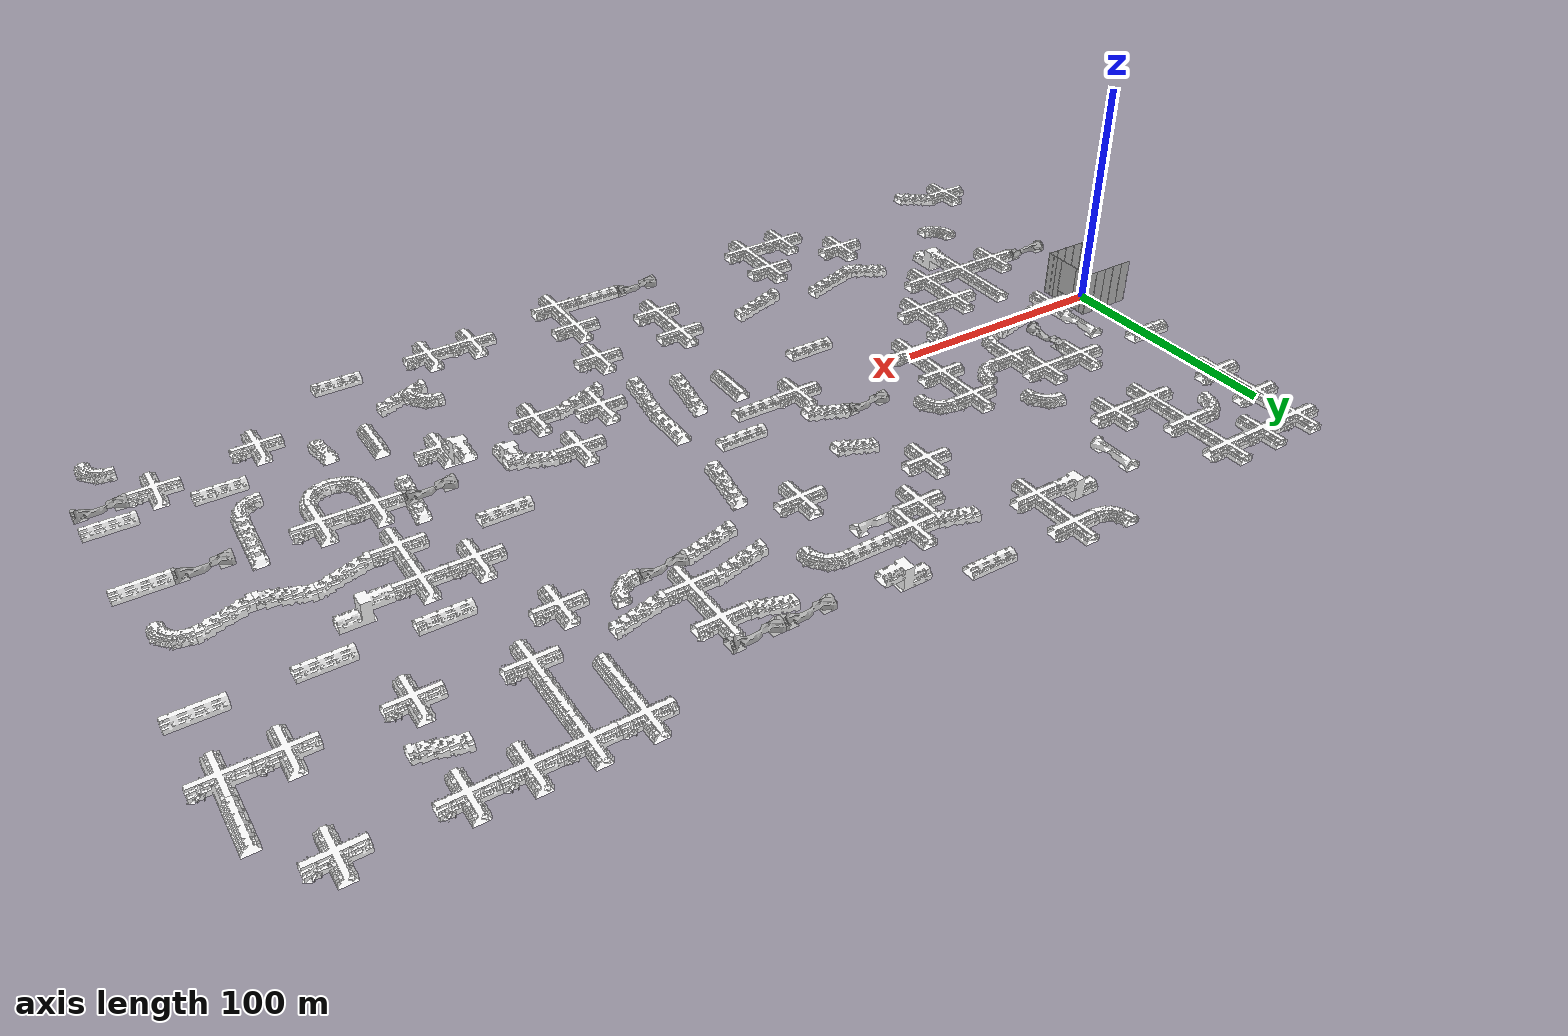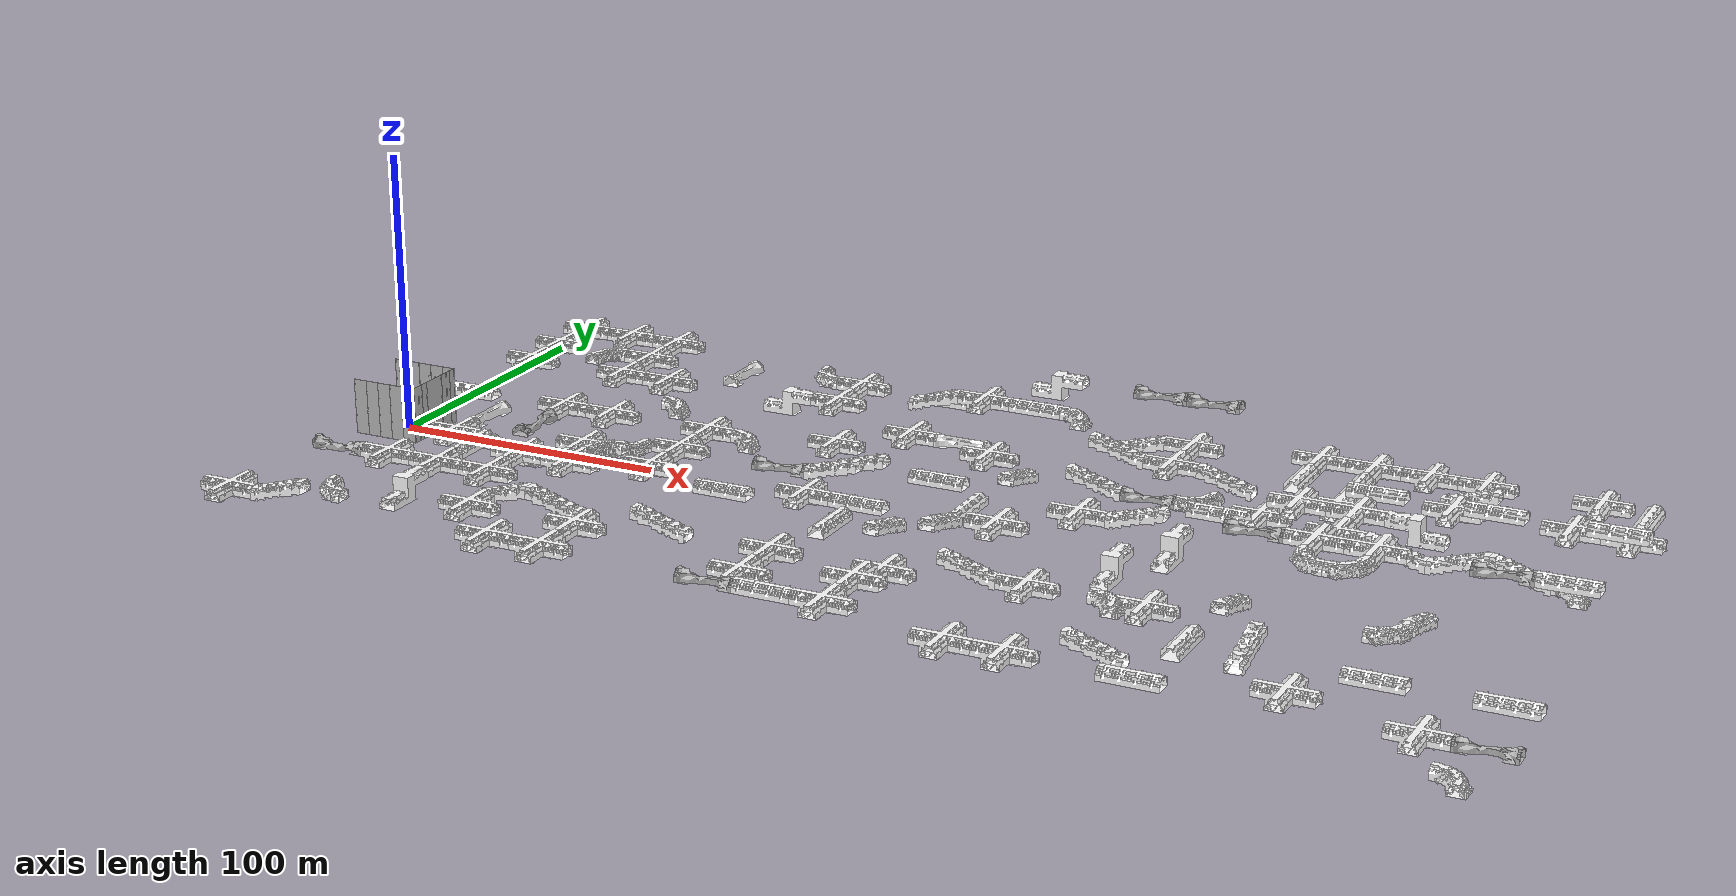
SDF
<sdf version="1.6">
 <world name="tunnel_circuit_practice_03">
  <physics name="1ms" type="ode">
   <max_step_size>0.004</max_step_size>
   <real_time_factor>1.0</real_time_factor>
  </physics>
  <scene>
   <ambient>1 1 1 1</ambient>
   <background>0.8 0.8 0.8 1</background>
   <shadows>true</shadows>
   <grid>true</grid>
   <origin_visual>true</origin_visual>
  </scene>
  <include><static>true</static><name>staging_area</name><uri>model://subt_tunnel_staging_area</uri></include>
  <include>
   <name>tile_1</name>
   <uri>model://Rough Tunnel Tile 4-way Intersection</uri>
   <pose>0.000000 120.000000 0.000000 0 0 0.000000</pose>
  </include>
  <include>
   <name>tile_4</name>
   <uri>model://Rough Tunnel Tile 4-way Intersection</uri>
   <pose>20.000000 120.000000 0.000000 0 0 0.000000</pose>
  </include>
  <include>
   <name>tile_7</name>
   <uri>model://Rough Tunnel Tile 4-way Intersection</uri>
   <pose>40.000000 120.000000 0.000000 0 0 0.000000</pose>
  </include>
  <include>
   <name>tile_12</name>
   <uri>model://Rough Tunnel Tile 90-degree Turn</uri>
   <pose>100.000000 120.000000 -5.000000 0 0 1.570796</pose>
  </include>
  <include>
   <name>tile_14</name>
   <uri>model://Rough Tunnel Tile 4-way Intersection</uri>
   <pose>120.000000 120.000000 -5.000000 0 0 0.000000</pose>
  </include>
  <include>
   <name>tile_19</name>
   <uri>model://Tunnel Tile 5</uri>
   <pose>160.000000 120.000000 -5.000000 0 0 1.570796</pose>
  </include>
  <include>
   <name>tile_24</name>
   <uri>model://Tunnel Tile 7</uri>
   <pose>200.000000 120.000000 5.000000 0 0 4.712389</pose>
  </include>
  <include>
   <name>tile_28</name>
   <uri>model://Constrained Tunnel Tile Short</uri>
   <pose>240.000000 120.000000 10.000000 0 0 1.570796</pose>
  </include>
  <include>
   <name>tile_29</name>
   <uri>model://Constrained Tunnel Tile Short</uri>
   <pose>260.000000 120.000000 10.000000 0 0 1.570796</pose>
  </include>
  <include>
   <name>tile_32</name>
   <uri>model://Rough Tunnel Tile 4-way Intersection</uri>
   <pose>300.000000 120.000000 -5.000000 0 0 0.000000</pose>
  </include>
  <include>
   <name>tile_35</name>
   <uri>model://Rough Tunnel Tile 4-way Intersection</uri>
   <pose>320.000000 120.000000 -5.000000 0 0 0.000000</pose>
  </include>
  <include>
   <name>tile_37</name>
   <uri>model://Rough Tunnel Tile 4-way Intersection</uri>
   <pose>340.000000 120.000000 -5.000000 0 0 0.000000</pose>
  </include>
  <include>
   <name>tile_39</name>
   <uri>model://Rough Tunnel Tile 4-way Intersection</uri>
   <pose>360.000000 120.000000 -5.000000 0 0 0.000000</pose>
  </include>
  <include>
   <name>tile_45</name>
   <uri>model://Rough Tunnel Tile 4-way Intersection</uri>
   <pose>400.000000 120.000000 -5.000000 0 0 0.000000</pose>
  </include>
  <include>
   <name>tile_50</name>
   <uri>model://Rough Tunnel Tile 4-way Intersection</uri>
   <pose>0.000000 100.000000 0.000000 0 0 0.000000</pose>
  </include>
  <include>
   <name>tile_53</name>
   <uri>model://Rough Tunnel Tile 90-degree Turn</uri>
   <pose>20.000000 100.000000 0.000000 0 0 0.000000</pose>
  </include>
  <include>
   <name>tile_54</name>
   <uri>model://Rough Tunnel Tile 4-way Intersection</uri>
   <pose>40.000000 100.000000 0.000000 0 0 0.000000</pose>
  </include>
  <include>
   <name>tile_57</name>
   <uri>model://Constrained Tunnel Tile Tall</uri>
   <pose>80.000000 100.000000 0.000000 0 0 3.141593</pose>
  </include>
  <include>
   <name>tile_58</name>
   <uri>model://Tunnel Tile 7</uri>
   <pose>100.000000 100.000000 -10.000000 0 0 4.712389</pose>
  </include>
  <include>
   <name>tile_60</name>
   <uri>model://Rough Tunnel Tile 4-way Intersection</uri>
   <pose>120.000000 100.000000 -5.000000 0 0 0.000000</pose>
  </include>
  <include>
   <name>tile_62</name>
   <uri>model://Tunnel Tile 6</uri>
   <pose>160.000000 100.000000 0.000000 0 0 4.712389</pose>
  </include>
  <include>
   <name>tile_63</name>
   <uri>model://Rough Tunnel Tile 4-way Intersection</uri>
   <pose>180.000000 100.000000 5.000000 0 0 0.000000</pose>
  </include>
  <include>
   <name>tile_65</name>
   <uri>model://Tunnel Tile 5</uri>
   <pose>200.000000 100.000000 5.000000 0 0 1.570796</pose>
  </include>
  <include>
   <name>tile_66</name>
   <uri>model://Rough Tunnel Tile 90-degree Turn</uri>
   <pose>220.000000 100.000000 5.000000 0 0 4.712389</pose>
  </include>
  <include>
   <name>tile_67</name>
   <uri>model://Tunnel Tile 6</uri>
   <pose>240.000000 100.000000 -5.000000 0 0 4.712389</pose>
  </include>
  <include>
   <name>tile_69</name>
   <uri>model://Rough Tunnel Tile 4-way Intersection</uri>
   <pose>260.000000 100.000000 0.000000 0 0 0.000000</pose>
  </include>
  <include>
   <name>tile_73</name>
   <uri>model://Tunnel Tile 5</uri>
   <pose>300.000000 100.000000 -5.000000 0 0 3.141593</pose>
  </include>
  <include>
   <name>tile_74</name>
   <uri>model://Tunnel Tile 5</uri>
   <pose>320.000000 100.000000 -5.000000 0 0 3.141593</pose>
  </include>
  <include>
   <name>tile_77</name>
   <uri>model://Tunnel Tile 6</uri>
   <pose>360.000000 100.000000 -5.000000 0 0 4.712389</pose>
  </include>
  <include>
   <name>tile_82</name>
   <uri>model://Tunnel Tile 5</uri>
   <pose>420.000000 100.000000 0.000000 0 0 3.141593</pose>
  </include>
  <include>
   <name>tile_84</name>
   <uri>model://Rough Tunnel Tile 4-way Intersection</uri>
   <pose>0.000000 80.000000 0.000000 0 0 0.000000</pose>
  </include>
  <include>
   <name>tile_87</name>
   <uri>model://Rough Tunnel Tile 4-way Intersection</uri>
   <pose>40.000000 80.000000 0.000000 0 0 0.000000</pose>
  </include>
  <include>
   <name>tile_88</name>
   <uri>model://Rough Tunnel Tile 4-way Intersection</uri>
   <pose>60.000000 80.000000 0.000000 0 0 0.000000</pose>
  </include>
  <include>
   <name>tile_96</name>
   <uri>model://Rough Tunnel Tile 4-way Intersection</uri>
   <pose>160.000000 80.000000 -5.000000 0 0 0.000000</pose>
  </include>
  <include>
   <name>tile_99</name>
   <uri>model://Constrained Tunnel Tile Tall</uri>
   <pose>180.000000 80.000000 -5.000000 0 0 1.570796</pose>
  </include>
  <include>
   <name>tile_105</name>
   <uri>model://Tunnel Tile 6</uri>
   <pose>240.000000 80.000000 0.000000 0 0 1.570796</pose>
  </include>
  <include>
   <name>tile_106</name>
   <uri>model://Rough Tunnel Tile 4-way Intersection</uri>
   <pose>260.000000 80.000000 0.000000 0 0 0.000000</pose>
  </include>
  <include>
   <name>tile_108</name>
   <uri>model://Tunnel Tile 6</uri>
   <pose>280.000000 80.000000 -5.000000 0 0 1.570796</pose>
  </include>
  <include>
   <name>tile_110</name>
   <uri>model://Rough Tunnel Tile 4-way Intersection</uri>
   <pose>320.000000 80.000000 -5.000000 0 0 0.000000</pose>
  </include>
  <include>
   <name>tile_113</name>
   <uri>model://Rough Tunnel Tile 4-way Intersection</uri>
   <pose>360.000000 80.000000 0.000000 0 0 0.000000</pose>
  </include>
  <include>
   <name>tile_119</name>
   <uri>model://Rough Tunnel Tile 4-way Intersection</uri>
   <pose>400.000000 80.000000 0.000000 0 0 0.000000</pose>
  </include>
  <include>
   <name>tile_122</name>
   <uri>model://Rough Tunnel Tile 4-way Intersection</uri>
   <pose>420.000000 80.000000 0.000000 0 0 0.000000</pose>
  </include>
  <include>
   <name>tile_131</name>
   <uri>model://Rough Tunnel Tile 90-degree Turn</uri>
   <pose>80.000000 60.000000 0.000000 0 0 4.712389</pose>
  </include>
  <include>
   <name>tile_137</name>
   <uri>model://Rough Tunnel Tile 4-way Intersection</uri>
   <pose>140.000000 60.000000 -5.000000 0 0 0.000000</pose>
  </include>
  <include>
   <name>tile_141</name>
   <uri>model://Rough Tunnel Tile 4-way Intersection</uri>
   <pose>200.000000 60.000000 0.000000 0 0 0.000000</pose>
  </include>
  <include>
   <name>tile_145</name>
   <uri>model://Tunnel Tile 6</uri>
   <pose>240.000000 60.000000 -5.000000 0 0 1.570796</pose>
  </include>
  <include>
   <name>tile_146</name>
   <uri>model://Constrained Tunnel Tile Short</uri>
   <pose>260.000000 60.000000 -5.000000 0 0 1.570796</pose>
  </include>
  <include>
   <name>tile_147</name>
   <uri>model://Rough Tunnel Tile 90-degree Turn</uri>
   <pose>280.000000 60.000000 -5.000000 0 0 3.141593</pose>
  </include>
  <include>
   <name>tile_149</name>
   <uri>model://Rough Tunnel Tile 4-way Intersection</uri>
   <pose>300.000000 60.000000 -5.000000 0 0 0.000000</pose>
  </include>
  <include>
   <name>tile_156</name>
   <uri>model://Tunnel Tile 5</uri>
   <pose>340.000000 60.000000 10.000000 0 0 1.570796</pose>
  </include>
  <include>
   <name>tile_158</name>
   <uri>model://Tunnel Tile 5</uri>
   <pose>380.000000 60.000000 10.000000 0 0 1.570796</pose>
  </include>
  <include>
   <name>tile_160</name>
   <uri>model://Tunnel Tile 5</uri>
   <pose>420.000000 60.000000 10.000000 0 0 1.570796</pose>
  </include>
  <include>
   <name>tile_162</name>
   <uri>model://Tunnel Tile 5</uri>
   <pose>0.000000 40.000000 0.000000 0 0 4.712389</pose>
  </include>
  <include>
   <name>tile_165</name>
   <uri>model://Rough Tunnel Tile 4-way Intersection</uri>
   <pose>40.000000 40.000000 0.000000 0 0 0.000000</pose>
  </include>
  <include>
   <name>tile_166</name>
   <uri>model://Rough Tunnel Tile 4-way Intersection</uri>
   <pose>60.000000 40.000000 0.000000 0 0 0.000000</pose>
  </include>
  <include>
   <name>tile_170</name>
   <uri>model://Rough Tunnel Tile 4-way Intersection</uri>
   <pose>100.000000 40.000000 0.000000 0 0 0.000000</pose>
  </include>
  <include>
   <name>tile_171</name>
   <uri>model://Rough Tunnel Tile 90-degree Turn</uri>
   <pose>120.000000 40.000000 0.000000 0 0 4.712389</pose>
  </include>
  <include>
   <name>tile_176</name>
   <uri>model://Tunnel Tile 6</uri>
   <pose>160.000000 40.000000 -5.000000 0 0 4.712389</pose>
  </include>
  <include>
   <name>tile_183</name>
   <uri>model://Tunnel Tile 6</uri>
   <pose>220.000000 40.000000 0.000000 0 0 3.141593</pose>
  </include>
  <include>
   <name>tile_188</name>
   <uri>model://Rough Tunnel Tile 4-way Intersection</uri>
   <pose>320.000000 40.000000 10.000000 0 0 0.000000</pose>
  </include>
  <include>
   <name>tile_189</name>
   <uri>model://Rough Tunnel Tile 4-way Intersection</uri>
   <pose>340.000000 40.000000 10.000000 0 0 0.000000</pose>
  </include>
  <include>
   <name>tile_191</name>
   <uri>model://Tunnel Tile 7</uri>
   <pose>360.000000 40.000000 5.000000 0 0 1.570796</pose>
  </include>
  <include>
   <name>tile_197</name>
   <uri>model://Constrained Tunnel Tile Tall</uri>
   <pose>20.000000 20.000000 0.000000 0 0 3.141593</pose>
  </include>
  <include>
   <name>tile_198</name>
   <uri>model://Constrained Tunnel Tile Short</uri>
   <pose>40.000000 20.000000 0.000000 0 0 0.000000</pose>
  </include>
  <include>
   <name>tile_200</name>
   <uri>model://Rough Tunnel Tile 4-way Intersection</uri>
   <pose>60.000000 20.000000 -5.000000 0 0 0.000000</pose>
  </include>
  <include>
   <name>tile_203</name>
   <uri>model://Rough Tunnel Tile 90-degree Turn</uri>
   <pose>80.000000 20.000000 -5.000000 0 0 3.141593</pose>
  </include>
  <include>
   <name>tile_205</name>
   <uri>model://Rough Tunnel Tile 4-way Intersection</uri>
   <pose>100.000000 20.000000 0.000000 0 0 0.000000</pose>
  </include>
  <include>
   <name>tile_208</name>
   <uri>model://Constrained Tunnel Tile Short</uri>
   <pose>140.000000 20.000000 0.000000 0 0 1.570796</pose>
  </include>
  <include>
   <name>tile_209</name>
   <uri>model://Tunnel Tile 6</uri>
   <pose>160.000000 20.000000 0.000000 0 0 4.712389</pose>
  </include>
  <include>
   <name>tile_211</name>
   <uri>model://Tunnel Tile 5</uri>
   <pose>200.000000 20.000000 5.000000 0 0 1.570796</pose>
  </include>
  <include>
   <name>tile_217</name>
   <uri>model://Tunnel Tile 5</uri>
   <pose>300.000000 20.000000 10.000000 0 0 1.570796</pose>
  </include>
  <include>
   <name>tile_220</name>
   <uri>model://Rough Tunnel Tile 4-way Intersection</uri>
   <pose>340.000000 20.000000 10.000000 0 0 0.000000</pose>
  </include>
  <include>
   <name>tile_222</name>
   <uri>model://Tunnel Tile 6</uri>
   <pose>360.000000 20.000000 5.000000 0 0 1.570796</pose>
  </include>
  <include>
   <name>tile_223</name>
   <uri>model://Tunnel Tile 6</uri>
   <pose>380.000000 20.000000 5.000000 0 0 4.712389</pose>
  </include>
  <include>
   <name>tile_224</name>
   <uri>model://Tunnel Tile 6</uri>
   <pose>400.000000 20.000000 5.000000 0 0 1.570796</pose>
  </include>
  <include>
   <name>tile_225</name>
   <uri>model://Rough Tunnel Tile 90-degree Turn</uri>
   <pose>420.000000 20.000000 5.000000 0 0 4.712389</pose>
  </include>
  <include>
   <name>tile_227</name>
   <uri>model://Rough Tunnel Tile 4-way Intersection</uri>
   <pose>20.000000 0.000000 0.000000 0 0 0.000000</pose>
  </include>
  <include>
   <name>tile_228</name>
   <uri>model://Tunnel Tile 6</uri>
   <pose>40.000000 0.000000 -5.000000 0 0 1.570796</pose>
  </include>
  <include>
   <name>tile_229</name>
   <uri>model://Rough Tunnel Tile 90-degree Turn</uri>
   <pose>60.000000 0.000000 -5.000000 0 0 3.141593</pose>
  </include>
  <include>
   <name>tile_230</name>
   <uri>model://Rough Tunnel Tile 90-degree Turn</uri>
   <pose>80.000000 0.000000 5.000000 0 0 0.000000</pose>
  </include>
  <include>
   <name>tile_232</name>
   <uri>model://Rough Tunnel Tile 4-way Intersection</uri>
   <pose>100.000000 0.000000 0.000000 0 0 0.000000</pose>
  </include>
  <include>
   <name>tile_241</name>
   <uri>model://Rough Tunnel Tile 4-way Intersection</uri>
   <pose>160.000000 0.000000 0.000000 0 0 0.000000</pose>
  </include>
  <include>
   <name>tile_244</name>
   <uri>model://Tunnel Tile 5</uri>
   <pose>180.000000 0.000000 0.000000 0 0 1.570796</pose>
  </include>
  <include>
   <name>tile_248</name>
   <uri>model://Tunnel Tile 5</uri>
   <pose>220.000000 0.000000 5.000000 0 0 0.000000</pose>
  </include>
  <include>
   <name>tile_251</name>
   <uri>model://Rough Tunnel Tile 4-way Intersection</uri>
   <pose>260.000000 0.000000 10.000000 0 0 0.000000</pose>
  </include>
  <include>
   <name>tile_252</name>
   <uri>model://Tunnel Tile 6</uri>
   <pose>280.000000 0.000000 10.000000 0 0 4.712389</pose>
  </include>
  <include>
   <name>tile_255</name>
   <uri>model://Constrained Tunnel Tile Short</uri>
   <pose>320.000000 0.000000 15.000000 0 0 1.570796</pose>
  </include>
  <include>
   <name>tile_256</name>
   <uri>model://Rough Tunnel Tile 4-way Intersection</uri>
   <pose>340.000000 0.000000 15.000000 0 0 0.000000</pose>
  </include>
  <include>
   <name>tile_258</name>
   <uri>model://Rough Tunnel Tile 4-way Intersection</uri>
   <pose>360.000000 0.000000 15.000000 0 0 0.000000</pose>
  </include>
  <include>
   <name>tile_261</name>
   <uri>model://Constrained Tunnel Tile Short</uri>
   <pose>400.000000 0.000000 15.000000 0 0 1.570796</pose>
  </include>
  <include>
   <name>tile_262</name>
   <uri>model://Tunnel Tile 5</uri>
   <pose>420.000000 0.000000 15.000000 0 0 1.570796</pose>
  </include>
  <include>
   <name>tile_265</name>
   <uri>model://Tunnel Tile 5</uri>
   <pose>40.000000 -20.000000 5.000000 0 0 3.141593</pose>
  </include>
  <include>
   <name>tile_267</name>
   <uri>model://Rough Tunnel Tile 4-way Intersection</uri>
   <pose>60.000000 -20.000000 5.000000 0 0 0.000000</pose>
  </include>
  <include>
   <name>tile_270</name>
   <uri>model://Rough Tunnel Tile 4-way Intersection</uri>
   <pose>80.000000 -20.000000 5.000000 0 0 0.000000</pose>
  </include>
  <include>
   <name>tile_275</name>
   <uri>model://Tunnel Tile 5</uri>
   <pose>140.000000 -20.000000 5.000000 0 0 1.570796</pose>
  </include>
  <include>
   <name>tile_278</name>
   <uri>model://Tunnel Tile 5</uri>
   <pose>180.000000 -20.000000 0.000000 0 0 3.141593</pose>
  </include>
  <include>
   <name>tile_280</name>
   <uri>model://Tunnel Tile 6</uri>
   <pose>200.000000 -20.000000 0.000000 0 0 3.141593</pose>
  </include>
  <include>
   <name>tile_282</name>
   <uri>model://Tunnel Tile 6</uri>
   <pose>220.000000 -20.000000 5.000000 0 0 3.141593</pose>
  </include>
  <include>
   <name>tile_284</name>
   <uri>model://Rough Tunnel Tile 4-way Intersection</uri>
   <pose>240.000000 -20.000000 10.000000 0 0 0.000000</pose>
  </include>
  <include>
   <name>tile_289</name>
   <uri>model://Tunnel Tile 7</uri>
   <pose>280.000000 -20.000000 0.000000 0 0 0.000000</pose>
  </include>
  <include>
   <name>tile_291</name>
   <uri>model://Tunnel Tile 7</uri>
   <pose>300.000000 -20.000000 10.000000 0 0 0.000000</pose>
  </include>
  <include>
   <name>tile_293</name>
   <uri>model://Tunnel Tile 6</uri>
   <pose>320.000000 -20.000000 -5.000000 0 0 3.141593</pose>
  </include>
  <include>
   <name>tile_295</name>
   <uri>model://Rough Tunnel Tile 90-degree Turn</uri>
   <pose>340.000000 -20.000000 15.000000 0 0 1.570796</pose>
  </include>
  <include>
   <name>tile_296</name>
   <uri>model://Rough Tunnel Tile 90-degree Turn</uri>
   <pose>360.000000 -20.000000 15.000000 0 0 3.141593</pose>
  </include>
  <include>
   <name>tile_297</name>
   <uri>model://Tunnel Tile 6</uri>
   <pose>380.000000 -20.000000 0.000000 0 0 3.141593</pose>
  </include>
  <include>
   <name>tile_299</name>
   <uri>model://Constrained Tunnel Tile Short</uri>
   <pose>0.000000 -40.000000 5.000000 0 0 4.712389</pose>
  </include>
  <include>
   <name>tile_301</name>
   <uri>model://Rough Tunnel Tile 4-way Intersection</uri>
   <pose>20.000000 -40.000000 5.000000 0 0 0.000000</pose>
  </include>
  <include>
   <name>tile_302</name>
   <uri>model://Rough Tunnel Tile 4-way Intersection</uri>
   <pose>40.000000 -40.000000 5.000000 0 0 0.000000</pose>
  </include>
  <include>
   <name>tile_303</name>
   <uri>model://Rough Tunnel Tile 4-way Intersection</uri>
   <pose>60.000000 -40.000000 5.000000 0 0 0.000000</pose>
  </include>
  <include>
   <name>tile_319</name>
   <uri>model://Tunnel Tile 6</uri>
   <pose>240.000000 -40.000000 0.000000 0 0 1.570796</pose>
  </include>
  <include>
   <name>tile_320</name>
   <uri>model://Rough Tunnel Tile 4-way Intersection</uri>
   <pose>260.000000 -40.000000 0.000000 0 0 0.000000</pose>
  </include>
  <include>
   <name>tile_325</name>
   <uri>model://Rough Tunnel Tile 4-way Intersection</uri>
   <pose>300.000000 -40.000000 0.000000 0 0 0.000000</pose>
  </include>
  <include>
   <name>tile_333</name>
   <uri>model://Rough Tunnel Tile 90-degree Turn</uri>
   <pose>380.000000 -40.000000 5.000000 0 0 3.141593</pose>
  </include>
  <include>
   <name>tile_339</name>
   <uri>model://Tunnel Tile 7</uri>
   <pose>40.000000 -60.000000 0.000000 0 0 0.000000</pose>
  </include>
  <include>
   <name>tile_342</name>
   <uri>model://Tunnel Tile 6</uri>
   <pose>80.000000 -60.000000 5.000000 0 0 4.712389</pose>
  </include>
  <include>
   <name>tile_343</name>
   <uri>model://Tunnel Tile 6</uri>
   <pose>100.000000 -60.000000 5.000000 0 0 1.570796</pose>
  </include>
  <include>
   <name>tile_345</name>
   <uri>model://Tunnel Tile 6</uri>
   <pose>140.000000 -60.000000 5.000000 0 0 1.570796</pose>
  </include>
  <include>
   <name>tile_348</name>
   <uri>model://Rough Tunnel Tile 4-way Intersection</uri>
   <pose>180.000000 -60.000000 5.000000 0 0 0.000000</pose>
  </include>
  <include>
   <name>tile_353</name>
   <uri>model://Rough Tunnel Tile 4-way Intersection</uri>
   <pose>220.000000 -60.000000 5.000000 0 0 0.000000</pose>
  </include>
  <include>
   <name>tile_362</name>
   <uri>model://Rough Tunnel Tile 90-degree Turn</uri>
   <pose>300.000000 -60.000000 10.000000 0 0 4.712389</pose>
  </include>
  <include>
   <name>tile_364</name>
   <uri>model://Tunnel Tile 5</uri>
   <pose>320.000000 -60.000000 0.000000 0 0 3.141593</pose>
  </include>
  <include>
   <name>tile_365</name>
   <uri>model://Tunnel Tile 6</uri>
   <pose>340.000000 -60.000000 0.000000 0 0 0.000000</pose>
  </include>
  <include>
   <name>tile_370</name>
   <uri>model://Tunnel Tile 5</uri>
   <pose>380.000000 -60.000000 0.000000 0 0 1.570796</pose>
  </include>
  <include>
   <name>tile_372</name>
   <uri>model://Tunnel Tile 5</uri>
   <pose>420.000000 -60.000000 0.000000 0 0 1.570796</pose>
  </include>
  <include>
   <name>tile_375</name>
   <uri>model://Rough Tunnel Tile 90-degree Turn</uri>
   <pose>20.000000 -80.000000 5.000000 0 0 1.570796</pose>
  </include>
  <include>
   <name>tile_380</name>
   <uri>model://Rough Tunnel Tile 4-way Intersection</uri>
   <pose>80.000000 -80.000000 10.000000 0 0 0.000000</pose>
  </include>
  <include>
   <name>tile_384</name>
   <uri>model://Rough Tunnel Tile 4-way Intersection</uri>
   <pose>120.000000 -80.000000 10.000000 0 0 0.000000</pose>
  </include>
  <include>
   <name>tile_390</name>
   <uri>model://Rough Tunnel Tile 4-way Intersection</uri>
   <pose>180.000000 -80.000000 5.000000 0 0 0.000000</pose>
  </include>
  <include>
   <name>tile_394</name>
   <uri>model://Rough Tunnel Tile 4-way Intersection</uri>
   <pose>220.000000 -80.000000 10.000000 0 0 0.000000</pose>
  </include>
  <include>
   <name>tile_400</name>
   <uri>model://Tunnel Tile 6</uri>
   <pose>300.000000 -80.000000 0.000000 0 0 1.570796</pose>
  </include>
  <include>
   <name>tile_405</name>
   <uri>model://Rough Tunnel Tile 4-way Intersection</uri>
   <pose>360.000000 -80.000000 0.000000 0 0 0.000000</pose>
  </include>
  <include>
   <name>tile_407</name>
   <uri>model://Rough Tunnel Tile 4-way Intersection</uri>
   <pose>400.000000 -80.000000 -5.000000 0 0 0.000000</pose>
  </include>
  <include>
   <name>tile_409</name>
   <uri>model://Constrained Tunnel Tile Short</uri>
   <pose>420.000000 -80.000000 -5.000000 0 0 1.570796</pose>
  </include>
  <include>
   <name>tile_411</name>
   <uri>model://Rough Tunnel Tile 4-way Intersection</uri>
   <pose>0.000000 -100.000000 10.000000 0 0 0.000000</pose>
  </include>
  <include>
   <name>tile_414</name>
   <uri>model://Tunnel Tile 6</uri>
   <pose>20.000000 -100.000000 10.000000 0 0 4.712389</pose>
  </include>
  <include>
   <name>tile_422</name>
   <uri>model://Rough Tunnel Tile 4-way Intersection</uri>
   <pose>100.000000 -100.000000 10.000000 0 0 0.000000</pose>
  </include>
  <include>
   <name>tile_424</name>
   <uri>model://Rough Tunnel Tile 4-way Intersection</uri>
   <pose>120.000000 -100.000000 10.000000 0 0 0.000000</pose>
  </include>
  <include>
   <name>tile_431</name>
   <uri>model://Constrained Tunnel Tile Short</uri>
   <pose>180.000000 -100.000000 10.000000 0 0 1.570796</pose>
  </include>
  <include>
   <name>tile_432</name>
   <uri>model://Tunnel Tile 5</uri>
   <pose>200.000000 -100.000000 10.000000 0 0 1.570796</pose>
  </include>
  <include>
   <name>tile_433</name>
   <uri>model://Rough Tunnel Tile 4-way Intersection</uri>
   <pose>220.000000 -100.000000 10.000000 0 0 0.000000</pose>
  </include>
  <include>
   <name>tile_437</name>
   <uri>model://Rough Tunnel Tile 4-way Intersection</uri>
   <pose>260.000000 -100.000000 5.000000 0 0 0.000000</pose>
  </include>
  <include>
   <name>tile_441</name>
   <uri>model://Rough Tunnel Tile 4-way Intersection</uri>
   <pose>280.000000 -100.000000 5.000000 0 0 0.000000</pose>
  </include>
  <include>
   <name>tile_446</name>
   <uri>model://Tunnel Tile 5</uri>
   <pose>320.000000 -100.000000 5.000000 0 0 1.570796</pose>
  </include>
  <include>
   <name>tile_455</name>
   <uri>model://Rough Tunnel Tile 90-degree Turn</uri>
   <pose>420.000000 -100.000000 -5.000000 0 0 4.712389</pose>
  </include>
 </world>
</sdf>

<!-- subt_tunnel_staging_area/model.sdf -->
<sdf version="1.6">
    <model name="subt_tunnel_staging_area">
        <static>true</static>
        <link name="link">
            <collision name="collision1">
                <pose>-10 -10 20 0 0 0</pose>
                <geometry>
                    <box>
                        <size>0.1 0.1 0.1</size>
                    </box>
                </geometry>
            </collision>
            <collision name="collision2">
                <pose>10 10 20 0 0 0</pose>
                <geometry>
                    <box>
                        <size>0.1 0.1 0.1</size>
                    </box>
                </geometry>
            </collision>
            <!-- The flat area where the robots starts -->
            <visual name="plane_visual">
                <pose>-1.181716 0 0 0 0 0</pose>
                <geometry>
                    <mesh>
                      <uri>model://subt_tunnel_staging_area/meshes/Asphalt_Plane.DAE</uri>
                    </mesh>
                </geometry>
            </visual>
            <visual name="fence_right1">
                <pose>8.818284 -12.4 0 1.5707 0 0</pose>
                <geometry>
                    <mesh>
                      <uri>model://subt_tunnel_staging_area/meshes/Fence.dae</uri>
                        <scale>1 6.7 1</scale>
                    </mesh>
                </geometry>
            </visual>
            <visual name="fence_right2">
                <pose>3.818284 -12.4 0 1.5707 0 0</pose>
                <geometry>
                    <mesh>
                      <uri>model://subt_tunnel_staging_area/meshes/Fence.dae</uri>
                        <scale>1 6.7 1</scale>
                    </mesh>
                </geometry>
            </visual>
            <visual name="fence_right3">
                <pose>-1.181716 -12.4 0 1.5707 0 0</pose>
                <geometry>
                    <mesh>
                      <uri>model://subt_tunnel_staging_area/meshes/Fence.dae</uri>
                        <scale>1 6.7 1</scale>
                    </mesh>
                </geometry>
            </visual>
            <visual name="fence_right4">
                <pose>-6.181716 -12.4 0 1.5707 0 0</pose>
                <geometry>
                    <mesh>
                      <uri>model://subt_tunnel_staging_area/meshes/Fence.dae</uri>
                        <scale>1 6.7 1</scale>
                    </mesh>
                </geometry>
            </visual>
            <visual name="fence_right5">
                <pose>-11.181716 -12.4 0 1.5707 0 0</pose>
                <geometry>
                    <mesh>
                      <uri>model://subt_tunnel_staging_area/meshes/Fence.dae</uri>
                        <scale>1 6.7 1</scale>
                    </mesh>
                </geometry>
            </visual>

            <visual name="fence_left1">
                <pose>8.818284 12.4 0 1.5707 0 3.1415</pose>
                <geometry>
                    <mesh>
                      <uri>model://subt_tunnel_staging_area/meshes/Fence.dae</uri>
                        <scale>1 6.7 1</scale>
                    </mesh>
                </geometry>
            </visual>
            <visual name="fence_left2">
                <pose>3.818284 12.4 0 1.5707 0 3.1415</pose>
                <geometry>
                    <mesh>
                      <uri>model://subt_tunnel_staging_area/meshes/Fence.dae</uri>
                        <scale>1 6.7 1</scale>
                    </mesh>
                </geometry>
            </visual>
            <visual name="fence_left3">
                <pose>-1.181716 12.4 0 1.5707 0 3.1415</pose>
                <geometry>
                    <mesh>
                      <uri>model://subt_tunnel_staging_area/meshes/Fence.dae</uri>
                        <scale>1 6.7 1</scale>
                    </mesh>
                </geometry>
            </visual>
            <visual name="fence_left4">
                <pose>-6.181716 12.4 0 1.5707 0 3.1415</pose>
                <geometry>
                    <mesh>
                      <uri>model://subt_tunnel_staging_area/meshes/Fence.dae</uri>
                        <scale>1 6.7 1</scale>
                    </mesh>
                </geometry>
            </visual>
            <visual name="fence_left5">
                <pose>-11.181716 12.4 0 1.5707 0 3.1415</pose>
                <geometry>
                    <mesh>
                      <uri>model://subt_tunnel_staging_area/meshes/Fence.dae</uri>
                        <scale>1 6.7 1</scale>
                    </mesh>
                </geometry>
            </visual>

            <visual name="fence_front_left1">
                <pose>11.3181716 10 0 1.5707 0 1.5707</pose>
                <geometry>
                    <mesh>
                      <uri>model://subt_tunnel_staging_area/meshes/Fence.dae</uri>
                        <scale>1 6.7 1</scale>
                    </mesh>
                </geometry>
            </visual>
            <visual name="fence_front_left2">
                <pose>11.3181716 7 0 1.5707 0 1.5707</pose>
                <geometry>
                    <mesh>
                      <uri>model://subt_tunnel_staging_area/meshes/Fence.dae</uri>
                        <scale>1 6.7 1</scale>
                    </mesh>
                </geometry>
            </visual>
            <visual name="fence_front_right1">
                <pose>11.3181716 -10 0 1.5707 0 1.5707</pose>
                <geometry>
                    <mesh>
                      <uri>model://subt_tunnel_staging_area/meshes/Fence.dae</uri>
                        <scale>1 6.7 1</scale>
                    </mesh>
                </geometry>
            </visual>
            <visual name="fence_front_right2">
                <pose>11.3181716 -7 0 1.5707 0 1.5707</pose>
                <geometry>
                    <mesh>
                      <uri>model://subt_tunnel_staging_area/meshes/Fence.dae</uri>
                        <scale>1 6.7 1</scale>
                    </mesh>
                </geometry>
            </visual>
            <visual name="fence_front_top">
                <pose>11.3181716 0 4.5 1.5707 0 1.5707</pose>
                <geometry>
                    <mesh>
                      <uri>model://subt_tunnel_staging_area/meshes/Fence.dae</uri>
                        <scale>1.8 5.17 1</scale>
                    </mesh>
                </geometry>
            </visual>

            <collision name="ceiling_collision">
                <pose>-1.181716 0 20.5 0 0 0</pose>
                <geometry>
                    <box>
                        <size>25 25 1</size>
                    </box>
                </geometry>
            </collision>
            <collision name="right_collision">
                <pose>-1.181716 -13 10.5 0 0 0</pose>
                <geometry>
                    <box>
                        <size>25 1 21</size>
                    </box>
                </geometry>
            </collision>
            <collision name="left_collision">
                <pose>-1.181716 13 10.5 0 0 0</pose>
                <geometry>
                    <box>
                        <size>25 1 21</size>
                    </box>
                </geometry>
            </collision>
            <collision name="rear_collision">
                <pose>-13.6181716 0 10.5 0 0 0</pose>
                <geometry>
                    <box>
                        <size>1 25 21</size>
                    </box>
                </geometry>
            </collision>
            <collision name="front_left_collision">
                <pose>11.3181716 8.75 10.5 0 0 0</pose>
                <geometry>
                    <box>
                        <size>1 9.5 21</size>
                    </box>
                </geometry>
            </collision>
            <collision name="front_right_collision">
                <pose>11.3181716 -8.75 10.5 0 0 0</pose>
                <geometry>
                    <box>
                        <size>1 9.5 21</size>
                    </box>
                </geometry>
            </collision>
            <collision name="front_top_collision">
                <pose>11.3181716 0 12.5 0 0 0</pose>
                <geometry>
                    <box>
                        <size>1 8 15</size>
                    </box>
                </geometry>
            </collision>

            <collision name="plane_collision">
                <pose>-1.181716 0 -0.502 0 0 0</pose>
                <geometry>
                    <box>
                        <size>25 25 1</size>
                    </box>
                </geometry>
            </collision>
            <!-- Entry to the tunnel -->
            <collision name="collision">
                <pose>10 0 -0.001 0 0 -1.5707963267948966</pose>
                <geometry>
                    <mesh>
                        <scale>0.93 0.93 0.93</scale>
                        <uri>model://subt_tunnel_staging_area/meshes/Entrance.dae</uri>
                    </mesh>
                </geometry>
            </collision>
            <visual name="visual">
                <pose>10 0 -0.001 0 0 -1.5707963267948966</pose>
                <geometry>
                    <mesh>
                        <scale>0.93 0.93 0.93</scale>
                        <uri>model://subt_tunnel_staging_area/meshes/Entrance.dae</uri>
                    </mesh>
                </geometry>
            </visual>
        </link>
    </model>
</sdf>

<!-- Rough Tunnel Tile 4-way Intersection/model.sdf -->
<sdf version="1.6">
  <model name="Rough Tunnel Tile 4-way Intersection">
    <static>true</static>
    <link name="link">
      <collision name="collision">
        <geometry>
          <mesh>
            <uri>model://Rough Tunnel Tile 4-way Intersection/meshes/4way_intersection_collider.dae</uri>
          </mesh>
        </geometry>
      </collision>
      <collision name="collision_ground">
        <geometry>
          <box>
            <size>20 20 0.001</size>
          </box>
        </geometry>
      </collision>

      <!-- rough terrain tile -->
      <visual name="visual_rough_rocks">
        <geometry>
          <mesh>
            <uri>model://Rough Tunnel Tile 4-way Intersection/meshes/4way_intersection_rough_terrain.dae</uri>
            <submesh>
              <name>Rocks</name>
              <center>false</center>
            </submesh>
            <scale>1.005 1.005 1.0</scale>
          </mesh>
        </geometry>
        <material>
          <diffuse>1.0 1.0 1.0</diffuse>
          <specular>1.0 1.0 1.0</specular>
          <script>
              <uri>model://Rough Tunnel Tile 4-way Intersection/materials/scripts</uri>
              <uri>model://Rough Tunnel Tile 4-way Intersection/materials/textures</uri>
              <name>RoughTunnelTile/Rocks_Diffuse</name>
          </script>
        </material>
      </visual>
      <visual name="visual_rough_rock_pile">
        <geometry>
          <mesh>
            <uri>model://Rough Tunnel Tile 4-way Intersection/meshes/4way_intersection_rough_terrain.dae</uri>
            <submesh>
              <name>RockPile</name>
              <center>false</center>
            </submesh>
            <scale>1.005 1.005 1.0</scale>
          </mesh>
        </geometry>
        <material>
          <diffuse>1.0 1.0 1.0</diffuse>
          <specular>1.0 1.0 1.0</specular>
          <script>
              <uri>model://Rough Tunnel Tile 4-way Intersection/materials/scripts</uri>
              <uri>model://Rough Tunnel Tile 4-way Intersection/materials/textures</uri>
              <name>RoughTunnelTile/RockPile_Diffuse</name>
          </script>
        </material>
      </visual>
      <visual name="visual_rough_concrete">
        <geometry>
          <mesh>
            <uri>model://Rough Tunnel Tile 4-way Intersection/meshes/4way_intersection_rough_terrain.dae</uri>
            <submesh>
              <name>Concrete</name>
              <center>false</center>
            </submesh>
            <scale>1.005 1.005 1.0</scale>
          </mesh>
        </geometry>
        <material>
          <diffuse>1.0 1.0 1.0</diffuse>
          <specular>1.0 1.0 1.0</specular>
          <script>
              <uri>model://Rough Tunnel Tile 4-way Intersection/materials/scripts</uri>
              <uri>model://Rough Tunnel Tile 4-way Intersection/materials/textures</uri>
              <name>RoughTunnelTile/ConcreteRubble_Diffuse</name>
          </script>
        </material>
      </visual>
      <visual name="visual_rough_wood">
        <geometry>
          <mesh>
            <uri>model://Rough Tunnel Tile 4-way Intersection/meshes/4way_intersection_rough_terrain.dae</uri>
            <submesh>
              <name>Wood</name>
              <center>false</center>
            </submesh>
            <scale>1.005 1.005 1.0</scale>
          </mesh>
        </geometry>
        <material>
          <diffuse>1.0 1.0 1.0</diffuse>
          <script>
              <uri>model://Rough Tunnel Tile 4-way Intersection/materials/scripts</uri>
              <uri>model://Rough Tunnel Tile 4-way Intersection/materials/textures</uri>
              <name>RoughTunnelTile/RoughWood_Diffuse</name>
          </script>
        </material>
      </visual>

      <!-- normal terrain tile -->
      <visual name="visual_chainlink">
        <geometry>
          <mesh>
            <uri>model://Rough Tunnel Tile 4-way Intersection/meshes/tunnel_tile_1.dae</uri>
            <submesh>
              <name>Chainlink</name>
              <center>false</center>
            </submesh>
            <scale>1.005 1.005 1.0</scale>
          </mesh>
        </geometry>
        <material>
          <diffuse>1.0 1.0 1.0</diffuse>
          <specular>1.0 1.0 1.0</specular>
          <script>
              <uri>model://Rough Tunnel Tile 4-way Intersection/materials/scripts</uri>
              <uri>model://Rough Tunnel Tile 4-way Intersection/materials/textures</uri>
              <name>TunnelTile/Chainlink_Diffuse</name>
          </script>
        </material>
      </visual>
      <visual name="visual_ground">
        <geometry>
          <mesh>
            <uri>model://Rough Tunnel Tile 4-way Intersection/meshes/tunnel_tile_1.dae</uri>
            <submesh>
              <name>Ground</name>
              <center>false</center>
            </submesh>
            <scale>1.005 1.005 1.0</scale>
          </mesh>
        </geometry>
        <material>
          <diffuse>1.0 1.0 1.0</diffuse>
          <specular>1.0 1.0 1.0</specular>
          <script>
              <uri>model://Rough Tunnel Tile 4-way Intersection/materials/scripts</uri>
              <uri>model://Rough Tunnel Tile 4-way Intersection/materials/textures</uri>
              <name>TunnelTile/Ground_Diffuse</name>
          </script>
        </material>
      </visual>
      <visual name="visual_wood">
        <geometry>
          <mesh>
            <uri>model://Rough Tunnel Tile 4-way Intersection/meshes/tunnel_tile_1.dae</uri>
            <submesh>
              <name>Wood</name>
              <center>false</center>
            </submesh>
            <scale>1.005 1.005 1.0</scale>
          </mesh>
        </geometry>
        <material>
          <diffuse>1.0 1.0 1.0</diffuse>
          <script>
              <uri>model://Rough Tunnel Tile 4-way Intersection/materials/scripts</uri>
              <uri>model://Rough Tunnel Tile 4-way Intersection/materials/textures</uri>
              <name>TunnelTile/Wood_Diffuse</name>
          </script>
        </material>
      </visual>
      <visual name="visual_walls">
        <geometry>
          <mesh>
            <uri>model://Rough Tunnel Tile 4-way Intersection/meshes/tunnel_tile_1.dae</uri>
            <submesh>
              <name>Walls</name>
              <center>false</center>
            </submesh>
            <scale>1.005 1.005 1.0</scale>
          </mesh>
        </geometry>
        <material>
          <diffuse>1.0 1.0 1.0</diffuse>
          <specular>1.0 1.0 1.0</specular>
          <script>
              <uri>model://Rough Tunnel Tile 4-way Intersection/materials/scripts</uri>
              <uri>model://Rough Tunnel Tile 4-way Intersection/materials/textures</uri>
              <name>TunnelTile/Walls_Diffuse</name>
          </script>
        </material>
      </visual>
      <visual name="visual_lights">
        <geometry>
          <mesh>
            <uri>model://Rough Tunnel Tile 4-way Intersection/meshes/tunnel_tile_1.dae</uri>
            <submesh>
              <name>Lights</name>
              <center>false</center>
            </submesh>
            <scale>1.005 1.005 1.0</scale>
          </mesh>
        </geometry>
        <material>
          <diffuse>1.0 1.0 1.0</diffuse>
          <specular>1.0 1.0 1.0</specular>
          <script>
              <uri>model://Rough Tunnel Tile 4-way Intersection/materials/scripts</uri>
              <uri>model://Rough Tunnel Tile 4-way Intersection/materials/textures</uri>
              <name>TunnelTile/Light_Diffuse</name>
          </script>
        </material>
      </visual>

    </link>
  </model>
</sdf>

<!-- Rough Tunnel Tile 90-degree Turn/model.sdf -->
<sdf version="1.6">
  <model name="Rough Tunnel Tile 90-degree Turn">
    <static>true</static>
    <link name="link">
      <collision name="collision">
        <geometry>
          <mesh>
            <uri>model://Rough Tunnel Tile 90-degree Turn/meshes/90deg_turn_collider.dae</uri>
          </mesh>
        </geometry>
      </collision>
      <collision name="collision_ground">
        <geometry>
          <box>
            <size>5 20 0.001</size>
          </box>
        </geometry>
      </collision>

      <!-- rough terrain tile -->
      <visual name="visual_rough_rocks">
        <geometry>
          <mesh>
            <uri>model://Rough Tunnel Tile 90-degree Turn/meshes/90deg_turn_rough_terrain.dae</uri>
            <submesh>
              <name>Rocks</name>
              <center>false</center>
            </submesh>
            <scale>1.005 1.005 1.0</scale>
          </mesh>
        </geometry>
        <material>
          <diffuse>1.0 1.0 1.0</diffuse>
          <specular>1.0 1.0 1.0</specular>
          <script>
              <uri>model://Rough Tunnel Tile 90-degree Turn/materials/scripts</uri>
              <uri>model://Rough Tunnel Tile 90-degree Turn/materials/textures</uri>
              <name>RoughTunnelTile/Rocks_Diffuse</name>
          </script>
        </material>
      </visual>
      <visual name="visual_rough_rock_pile">
        <geometry>
          <mesh>
            <uri>model://Rough Tunnel Tile 90-degree Turn/meshes/90deg_turn_rough_terrain.dae</uri>
            <submesh>
              <name>RockPile</name>
              <center>false</center>
            </submesh>
            <scale>1.005 1.005 1.0</scale>
          </mesh>
        </geometry>
        <material>
          <diffuse>1.0 1.0 1.0</diffuse>
          <specular>1.0 1.0 1.0</specular>
          <script>
              <uri>model://Rough Tunnel Tile 90-degree Turn/materials/scripts</uri>
              <uri>model://Rough Tunnel Tile 90-degree Turn/materials/textures</uri>
              <name>RoughTunnelTile/RockPile_Diffuse</name>
          </script>
        </material>
      </visual>
      <visual name="visual_rough_concrete">
        <geometry>
          <mesh>
            <uri>model://Rough Tunnel Tile 90-degree Turn/meshes/90deg_turn_rough_terrain.dae</uri>
            <submesh>
              <name>Concrete</name>
              <center>false</center>
            </submesh>
            <scale>1.005 1.005 1.0</scale>
          </mesh>
        </geometry>
        <material>
          <diffuse>1.0 1.0 1.0</diffuse>
          <specular>1.0 1.0 1.0</specular>
          <script>
              <uri>model://Rough Tunnel Tile 90-degree Turn/materials/scripts</uri>
              <uri>model://Rough Tunnel Tile 90-degree Turn/materials/textures</uri>
              <name>RoughTunnelTile/ConcreteRubble_Diffuse</name>
          </script>
        </material>
      </visual>
      <visual name="visual_rough_wood">
        <geometry>
          <mesh>
            <uri>model://Rough Tunnel Tile 90-degree Turn/meshes/90deg_turn_rough_terrain.dae</uri>
            <submesh>
              <name>Wood</name>
              <center>false</center>
            </submesh>
            <scale>1.005 1.005 1.0</scale>
          </mesh>
        </geometry>
        <material>
          <diffuse>1.0 1.0 1.0</diffuse>
          <script>
              <uri>model://Rough Tunnel Tile 90-degree Turn/materials/scripts</uri>
              <uri>model://Rough Tunnel Tile 90-degree Turn/materials/textures</uri>
              <name>RoughTunnelTile/RoughWood_Diffuse</name>
          </script>
        </material>
      </visual>

      <!-- normal terrain tile -->
      <visual name="visual_chainlink">
        <geometry>
          <mesh>
            <uri>model://Rough Tunnel Tile 90-degree Turn/meshes/tunnel_tile_2.dae</uri>
            <submesh>
              <name>Chainlink</name>
              <center>false</center>
            </submesh>
            <scale>1.005 1.005 1.0</scale>
          </mesh>
        </geometry>
        <material>
          <diffuse>1.0 1.0 1.0</diffuse>
          <specular>1.0 1.0 1.0</specular>
          <script>
              <uri>model://Rough Tunnel Tile 90-degree Turn/materials/scripts</uri>
              <uri>model://Rough Tunnel Tile 90-degree Turn/materials/textures</uri>
              <name>TunnelTile/Chainlink_Diffuse</name>
          </script>
        </material>
      </visual>
      <visual name="visual_ground">
        <geometry>
          <mesh>
            <uri>model://Rough Tunnel Tile 90-degree Turn/meshes/tunnel_tile_2.dae</uri>
            <submesh>
              <name>Ground</name>
              <center>false</center>
            </submesh>
            <scale>1.005 1.005 1.0</scale>
          </mesh>
        </geometry>
        <material>
          <diffuse>1.0 1.0 1.0</diffuse>
          <specular>1.0 1.0 1.0</specular>
          <script>
              <uri>model://Rough Tunnel Tile 90-degree Turn/materials/scripts</uri>
              <uri>model://Rough Tunnel Tile 90-degree Turn/materials/textures</uri>
              <name>TunnelTile/Ground_Diffuse</name>
          </script>
        </material>
      </visual>
      <visual name="visual_wood">
        <geometry>
          <mesh>
            <uri>model://Rough Tunnel Tile 90-degree Turn/meshes/tunnel_tile_2.dae</uri>
            <submesh>
              <name>Wood</name>
              <center>false</center>
            </submesh>
            <scale>1.005 1.005 1.0</scale>
          </mesh>
        </geometry>
        <material>
          <diffuse>1.0 1.0 1.0</diffuse>
          <script>
              <uri>model://Rough Tunnel Tile 90-degree Turn/materials/scripts</uri>
              <uri>model://Rough Tunnel Tile 90-degree Turn/materials/textures</uri>
              <name>TunnelTile/Wood_Diffuse</name>
          </script>
        </material>
      </visual>
      <visual name="visual_walls">
        <geometry>
          <mesh>
            <uri>model://Rough Tunnel Tile 90-degree Turn/meshes/tunnel_tile_2.dae</uri>
            <submesh>
              <name>Walls</name>
              <center>false</center>
            </submesh>
            <scale>1.005 1.005 1.0</scale>
          </mesh>
        </geometry>
        <material>
          <diffuse>1.0 1.0 1.0</diffuse>
          <specular>1.0 1.0 1.0</specular>
          <script>
              <uri>model://Rough Tunnel Tile 90-degree Turn/materials/scripts</uri>
              <uri>model://Rough Tunnel Tile 90-degree Turn/materials/textures</uri>
              <name>TunnelTile/Walls_Diffuse</name>
          </script>
        </material>
      </visual>
      <visual name="visual_lights">
        <geometry>
          <mesh>
            <uri>model://Rough Tunnel Tile 90-degree Turn/meshes/tunnel_tile_2.dae</uri>
            <submesh>
              <name>Lights</name>
              <center>false</center>
            </submesh>
            <scale>1.005 1.005 1.0</scale>
          </mesh>
        </geometry>
        <material>
          <diffuse>1.0 1.0 1.0</diffuse>
          <specular>1.0 1.0 1.0</specular>
          <script>
              <uri>model://Rough Tunnel Tile 90-degree Turn/materials/scripts</uri>
              <uri>model://Rough Tunnel Tile 90-degree Turn/materials/textures</uri>
              <name>TunnelTile/Light_Diffuse</name>
          </script>
        </material>
      </visual>

    </link>
  </model>
</sdf>

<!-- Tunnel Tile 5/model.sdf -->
<sdf version="1.6">
  <model name="Tunnel Tile 5">
    <static>true</static>
    <link name="link">
      <collision name="collision">
        <geometry>
          <mesh>
            <uri>model://Tunnel Tile 5/meshes/Tunnel Tile 5.dae</uri>
          </mesh>
        </geometry>
      </collision>
      <collision name="collision_ground">
        <geometry>
          <box>
            <size>5 20 0.001</size>
          </box>
        </geometry>
      </collision>
      <visual name="visual_chainlink">
        <geometry>
          <mesh>
            <uri>model://Tunnel Tile 5/meshes/Tunnel Tile 5.dae</uri>
            <submesh>
              <name>Chainlink</name>
              <center>false</center>
            </submesh>
            <scale>1.005 1.005 1.0</scale>
          </mesh>
        </geometry>
        <material>
          <diffuse>1.0 1.0 1.0</diffuse>
          <specular>1.0 1.0 1.0</specular>
          <script>
              <uri>model://Tunnel Tile 5/materials/scripts</uri>
              <uri>model://Tunnel Tile 5/materials/textures</uri>
              <name>TunnelTile/Chainlink_Diffuse</name>
          </script>
        </material>
      </visual>
      <visual name="visual_ground">
        <geometry>
          <mesh>
            <uri>model://Tunnel Tile 5/meshes/Tunnel Tile 5.dae</uri>
            <submesh>
              <name>Ground</name>
              <center>false</center>
            </submesh>
            <scale>1.005 1.005 1.0</scale>
          </mesh>
        </geometry>
        <material>
          <diffuse>1.0 1.0 1.0</diffuse>
          <specular>1.0 1.0 1.0</specular>
          <script>
              <uri>model://Tunnel Tile 5/materials/scripts</uri>
              <uri>model://Tunnel Tile 5/materials/textures</uri>
              <name>TunnelTile/Ground_Diffuse</name>
          </script>
        </material>
      </visual>
      <visual name="visual_wood">
        <geometry>
          <mesh>
            <uri>model://Tunnel Tile 5/meshes/Tunnel Tile 5.dae</uri>
            <submesh>
              <name>Wood</name>
              <center>false</center>
            </submesh>
            <scale>1.005 1.005 1.0</scale>
          </mesh>
        </geometry>
        <material>
          <diffuse>1.0 1.0 1.0</diffuse>
          <specular>1.0 1.0 1.0</specular>
          <script>
              <uri>model://Tunnel Tile 5/materials/scripts</uri>
              <uri>model://Tunnel Tile 5/materials/textures</uri>
              <name>TunnelTile/Wood_Diffuse</name>
          </script>
        </material>
      </visual>
      <visual name="visual_walls">
        <geometry>
          <mesh>
            <uri>model://Tunnel Tile 5/meshes/Tunnel Tile 5.dae</uri>
            <submesh>
              <name>Walls</name>
              <center>false</center>
            </submesh>
            <scale>1.005 1.005 1.0</scale>
          </mesh>
        </geometry>
        <material>
          <diffuse>1.0 1.0 1.0</diffuse>
          <specular>1.0 1.0 1.0</specular>
          <script>
              <uri>model://Tunnel Tile 5/materials/scripts</uri>
              <uri>model://Tunnel Tile 5/materials/textures</uri>
              <name>TunnelTile/Walls_Diffuse</name>
          </script>
        </material>
      </visual>
      <visual name="visual_lights">
        <geometry>
          <mesh>
            <uri>model://Tunnel Tile 5/meshes/Tunnel Tile 5.dae</uri>
            <submesh>
              <name>Lights</name>
              <center>false</center>
            </submesh>
            <scale>1.005 1.005 1.0</scale>
          </mesh>
        </geometry>
        <material>
          <diffuse>1.0 1.0 1.0</diffuse>
          <specular>1.0 1.0 1.0</specular>
          <script>
              <uri>model://Tunnel Tile 5/materials/scripts</uri>
              <uri>model://Tunnel Tile 5/materials/textures</uri>
              <name>TunnelTile/Light_Diffuse</name>
          </script>
        </material>
      </visual>
    </link>
  </model>
</sdf>

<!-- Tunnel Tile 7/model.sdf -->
<sdf version="1.6">
  <model name="Tunnel Tile 7">
    <static>true</static>
    <link name="link">
      <collision name="collision">
        <geometry>
          <mesh>
            <uri>model://Tunnel Tile 7/meshes/Tunnel Tile 7.dae</uri>
          </mesh>
        </geometry>
      </collision>
      <collision name="collision_ground_1">
        <pose>0 6.14028 5 0 0 0</pose>
        <geometry>
          <box>
            <size>6.19538 7.71943 0.001</size>
          </box>
        </geometry>
      </collision>
      <collision name="collision_ground_2">
        <pose>0 2.28057 2.5 0 0 0</pose>
        <geometry>
          <box>
            <size>6.19538 0.001 5</size>
          </box>
        </geometry>
      </collision>
      <collision name="collision_ground_3">
        <pose>0 -3.8572 0 0 0 0</pose>
        <geometry>
          <box>
            <size>6.19538 12.2806 0.001</size>
          </box>
        </geometry>
      </collision>
      <collision name="collision_ground_4">
        <pose>0 -2.42079 6.38525 0 0 0</pose>
        <geometry>
          <box>
            <size>6.19538 0.001 5.69769</size>
          </box>
        </geometry>
      </collision>
      <collision name="collision_ground_5">
        <pose>-2.83306 0.079873 4.58439 0 0 0</pose>
        <geometry>
          <box>
            <size>0.001 5.1333 9.16878</size>
          </box>
        </geometry>
      </collision>
      <collision name="collision_ground_6">
        <pose>2.83306 0.079873 4.58439 0 0 0</pose>
        <geometry>
          <box>
            <size>0.001 5.1333 9.16878</size>
          </box>
        </geometry>
      </collision>
      <collision name="collision_ground_7">
        <pose>0 0.079873 8.72854 0 0 0</pose>
        <geometry>
          <box>
            <size>6.95991 5.1333 0.001</size>
          </box>
        </geometry>
      </collision>
      <visual name="visual_chainlink">
        <geometry>
          <mesh>
            <uri>model://Tunnel Tile 7/meshes/Tunnel Tile 7.dae</uri>
            <submesh>
              <name>Chainlink</name>
              <center>false</center>
            </submesh>
            <scale>1.005 1.005 1.0</scale>
          </mesh>
        </geometry>
        <material>
          <diffuse>1.0 1.0 1.0</diffuse>
          <specular>1.0 1.0 1.0</specular>
          <script>
              <uri>model://Tunnel Tile 7/materials/scripts</uri>
              <uri>model://Tunnel Tile 7/materials/textures</uri>
              <name>TunnelTile/Chainlink_Diffuse</name>
          </script>
        </material>
      </visual>
      <visual name="visual_ground">
        <geometry>
          <mesh>
            <uri>model://Tunnel Tile 7/meshes/Tunnel Tile 7.dae</uri>
            <submesh>
              <name>Ground</name>
              <center>false</center>
            </submesh>
            <scale>1.005 1.005 1.0</scale>
          </mesh>
        </geometry>
        <material>
          <diffuse>1.0 1.0 1.0</diffuse>
          <specular>1.0 1.0 1.0</specular>
          <script>
              <uri>model://Tunnel Tile 7/materials/scripts</uri>
              <uri>model://Tunnel Tile 7/materials/textures</uri>
              <name>TunnelTile/Ground_Diffuse</name>
          </script>
        </material>
      </visual>
      <visual name="visual_wood">
        <geometry>
          <mesh>
            <uri>model://Tunnel Tile 7/meshes/Tunnel Tile 7.dae</uri>
            <submesh>
              <name>Wood</name>
              <center>false</center>
            </submesh>
            <scale>1.005 1.005 1.0</scale>
          </mesh>
        </geometry>
        <material>
          <diffuse>1.0 1.0 1.0</diffuse>
          <specular>1.0 1.0 1.0</specular>
          <script>
              <uri>model://Tunnel Tile 7/materials/scripts</uri>
              <uri>model://Tunnel Tile 7/materials/textures</uri>
              <name>TunnelTile/Wood_Diffuse</name>
          </script>
        </material>
      </visual>
      <visual name="visual_walls">
        <geometry>
          <mesh>
            <uri>model://Tunnel Tile 7/meshes/Tunnel Tile 7.dae</uri>
            <submesh>
              <name>Walls</name>
              <center>false</center>
            </submesh>
            <scale>1.005 1.005 1.0</scale>
          </mesh>
        </geometry>
        <material>
          <diffuse>1.0 1.0 1.0</diffuse>
          <specular>1.0 1.0 1.0</specular>
          <script>
              <uri>model://Tunnel Tile 7/materials/scripts</uri>
              <uri>model://Tunnel Tile 7/materials/textures</uri>
              <name>TunnelTile/Walls_Diffuse</name>
          </script>
        </material>
      </visual>
      <visual name="visual_lights">
        <geometry>
          <mesh>
            <uri>model://Tunnel Tile 7/meshes/Tunnel Tile 7.dae</uri>
            <submesh>
              <name>Lights</name>
              <center>false</center>
            </submesh>
            <scale>1.005 1.005 1.0</scale>
          </mesh>
        </geometry>
        <material>
          <diffuse>1.0 1.0 1.0</diffuse>
          <specular>1.0 1.0 1.0</specular>
          <script>
              <uri>model://Tunnel Tile 7/materials/scripts</uri>
              <uri>model://Tunnel Tile 7/materials/textures</uri>
              <name>TunnelTile/Light_Diffuse</name>
          </script>
        </material>
      </visual>
    </link>
  </model>
</sdf>

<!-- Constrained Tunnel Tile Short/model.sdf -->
<sdf version='1.6'>
  <model name='Constrained Tunnel Tile Short'>
    <pose>0 0 0 0 0 0</pose>
    <static>true</static>
    <link name="link">
      <collision name="collision">
        <geometry>
          <mesh>
            <uri>model://Constrained Tunnel Tile Short/meshes/Constrained Tunnel Tile Short.dae</uri>
         </mesh>
        </geometry>
      </collision>
      <visual name="visual">
        <geometry>
          <mesh>
            <uri>model://Constrained Tunnel Tile Short/meshes/Constrained Tunnel Tile Short.dae</uri>
         </mesh>
        </geometry>
      </visual>
    </link>
  </model>
 </sdf>

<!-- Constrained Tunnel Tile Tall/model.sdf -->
<sdf version="1.6">
  <model name="Constrained Tunnel Tile Tall">
    <static>true</static>
    <link name="link">
      <collision name="collision">
        <geometry>
          <mesh>
            <uri>model://Constrained Tunnel Tile Tall/meshes/constrained_tall.dae</uri>
          </mesh>
        </geometry>
      </collision>
      <collision name="collision_ground">
        <geometry>
          <box>
            <size>5 20 0.001</size>
          </box>
        </geometry>
      </collision>
      <visual name="visual_chainlink">
        <geometry>
          <mesh>
            <uri>model://Constrained Tunnel Tile Tall/meshes/constrained_tall.dae</uri>
            <submesh>
              <name>Chainlink</name>
              <center>false</center>
            </submesh>
            <scale>1.001 1.001 1.0</scale>
          </mesh>
        </geometry>
        <material>
          <diffuse>1.0 1.0 1.0</diffuse>
          <specular>1.0 1.0 1.0</specular>
          <script>
              <uri>model://Constrained Tunnel Tile Tall/materials/scripts</uri>
              <uri>model://Constrained Tunnel Tile Tall/materials/textures</uri>
              <name>TunnelTile/Chainlink_Diffuse</name>
          </script>
        </material>
      </visual>
      <visual name="visual_ground">
        <geometry>
          <mesh>
            <uri>model://Constrained Tunnel Tile Tall/meshes/constrained_tall.dae</uri>
            <submesh>
              <name>Ground</name>
              <center>false</center>
            </submesh>
            <scale>1.001 1.001 1.0</scale>
          </mesh>
        </geometry>
        <material>
          <diffuse>1.0 1.0 1.0</diffuse>
          <specular>1.0 1.0 1.0</specular>
          <script>
              <uri>model://Constrained Tunnel Tile Tall/materials/scripts</uri>
              <uri>model://Constrained Tunnel Tile Tall/materials/textures</uri>
              <name>TunnelTile/Ground_Diffuse</name>
          </script>
        </material>
      </visual>
      <visual name="visual_wood">
        <geometry>
          <mesh>
            <uri>model://Constrained Tunnel Tile Tall/meshes/constrained_tall.dae</uri>
            <submesh>
              <name>Wood</name>
              <center>false</center>
            </submesh>
            <scale>1.001 1.001 1.0</scale>
          </mesh>
        </geometry>
        <material>
          <diffuse>1.0 1.0 1.0</diffuse>
          <script>
              <uri>model://Constrained Tunnel Tile Tall/materials/scripts</uri>
              <uri>model://Constrained Tunnel Tile Tall/materials/textures</uri>
              <name>TunnelTile/Wood_Diffuse</name>
          </script>
        </material>
      </visual>
      <visual name="visual_walls">
        <geometry>
          <mesh>
            <uri>model://Constrained Tunnel Tile Tall/meshes/constrained_tall.dae</uri>
            <submesh>
              <name>Walls</name>
              <center>false</center>
            </submesh>
            <scale>1.001 1.001 1.0</scale>
          </mesh>
        </geometry>
        <material>
          <diffuse>1.0 1.0 1.0</diffuse>
          <specular>1.0 1.0 1.0</specular>
          <script>
              <uri>model://Constrained Tunnel Tile Tall/materials/scripts</uri>
              <uri>model://Constrained Tunnel Tile Tall/materials/textures</uri>
              <name>TunnelTile/Walls_Diffuse</name>
          </script>
        </material>
      </visual>
      <visual name="visual_dirt_wall">
        <geometry>
          <mesh>
            <uri>model://Constrained Tunnel Tile Tall/meshes/constrained_tall.dae</uri>
            <submesh>
              <name>DirtWall</name>
              <center>false</center>
            </submesh>
            <scale>1.001 1.001 1.0</scale>
          </mesh>
        </geometry>
        <material>
          <diffuse>1.0 1.0 1.0</diffuse>
          <specular>1.0 1.0 1.0</specular>
          <script>
              <uri>model://Constrained Tunnel Tile Tall/materials/scripts</uri>
              <uri>model://Constrained Tunnel Tile Tall/materials/textures</uri>
              <name>TunnelTile/ConstrainedWall_Diffuse</name>
          </script>
        </material>
      </visual>
    </link>
  </model>
</sdf>

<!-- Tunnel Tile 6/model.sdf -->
<sdf version="1.6">
  <model name="Tunnel Tile 6">
    <static>true</static>
    <link name="link">
      <pose>0 0 0 0 0 0</pose>
      <collision name="collision">
        <geometry>
          <mesh>
            <uri>model://Tunnel Tile 6/meshes/Tunnel Tile 6.dae</uri>
          </mesh>
        </geometry>
      </collision>
      <visual name="visual_chainlink">
        <geometry>
          <mesh>
            <uri>model://Tunnel Tile 6/meshes/Tunnel Tile 6.dae</uri>
            <submesh>
              <name>Chainlink</name>
              <center>false</center>
            </submesh>
            <scale>1.005 1.005 1.0</scale>
          </mesh>
        </geometry>
        <material>
          <diffuse>1.0 1.0 1.0</diffuse>
          <specular>1.0 1.0 1.0</specular>
          <script>
              <uri>model://Tunnel Tile 6/materials/scripts</uri>
              <uri>model://Tunnel Tile 6/materials/textures</uri>
              <name>TunnelTile/Chainlink_Diffuse</name>
          </script>
        </material>
      </visual>
      <visual name="visual_ground">
        <geometry>
          <mesh>
            <uri>model://Tunnel Tile 6/meshes/Tunnel Tile 6.dae</uri>
            <submesh>
              <name>Ground</name>
              <center>false</center>
            </submesh>
            <scale>1.005 1.005 1.0</scale>
          </mesh>
        </geometry>
        <material>
          <diffuse>1.0 1.0 1.0</diffuse>
          <specular>1.0 1.0 1.0</specular>
          <script>
              <uri>model://Tunnel Tile 6/materials/scripts</uri>
              <uri>model://Tunnel Tile 6/materials/textures</uri>
              <name>TunnelTile/Ground_Diffuse</name>
          </script>
        </material>
      </visual>
      <visual name="visual_wood">
        <geometry>
          <mesh>
            <uri>model://Tunnel Tile 6/meshes/Tunnel Tile 6.dae</uri>
            <submesh>
              <name>Wood</name>
              <center>false</center>
            </submesh>
            <scale>1.005 1.005 1.0</scale>
          </mesh>
        </geometry>
        <material>
          <diffuse>1.0 1.0 1.0</diffuse>
          <script>
              <uri>model://Tunnel Tile 6/materials/scripts</uri>
              <uri>model://Tunnel Tile 6/materials/textures</uri>
              <name>TunnelTile/Wood_Diffuse</name>
          </script>
        </material>
      </visual>
      <visual name="visual_walls">
        <geometry>
          <mesh>
            <uri>model://Tunnel Tile 6/meshes/Tunnel Tile 6.dae</uri>
            <submesh>
              <name>Walls</name>
              <center>false</center>
            </submesh>
            <scale>1.005 1.005 1.0</scale>
          </mesh>
        </geometry>
        <material>
          <diffuse>1.0 1.0 1.0</diffuse>
          <specular>1.0 1.0 1.0</specular>
          <script>
              <uri>model://Tunnel Tile 6/materials/scripts</uri>
              <uri>model://Tunnel Tile 6/materials/textures</uri>
              <name>TunnelTile/Walls_Diffuse</name>
          </script>
        </material>
      </visual>
      <visual name="visual_lights">
        <geometry>
          <mesh>
            <uri>model://Tunnel Tile 6/meshes/Tunnel Tile 6.dae</uri>
            <submesh>
              <name>Lights</name>
              <center>false</center>
            </submesh>
            <scale>1.005 1.005 1.0</scale>
          </mesh>
        </geometry>
        <material>
          <diffuse>1.0 1.0 1.0</diffuse>
          <specular>1.0 1.0 1.0</specular>
          <script>
              <uri>model://Tunnel Tile 6/materials/scripts</uri>
              <uri>model://Tunnel Tile 6/materials/textures</uri>
              <name>TunnelTile/Light_Diffuse</name>
          </script>
        </material>
      </visual>
    </link>
  </model>
</sdf>
